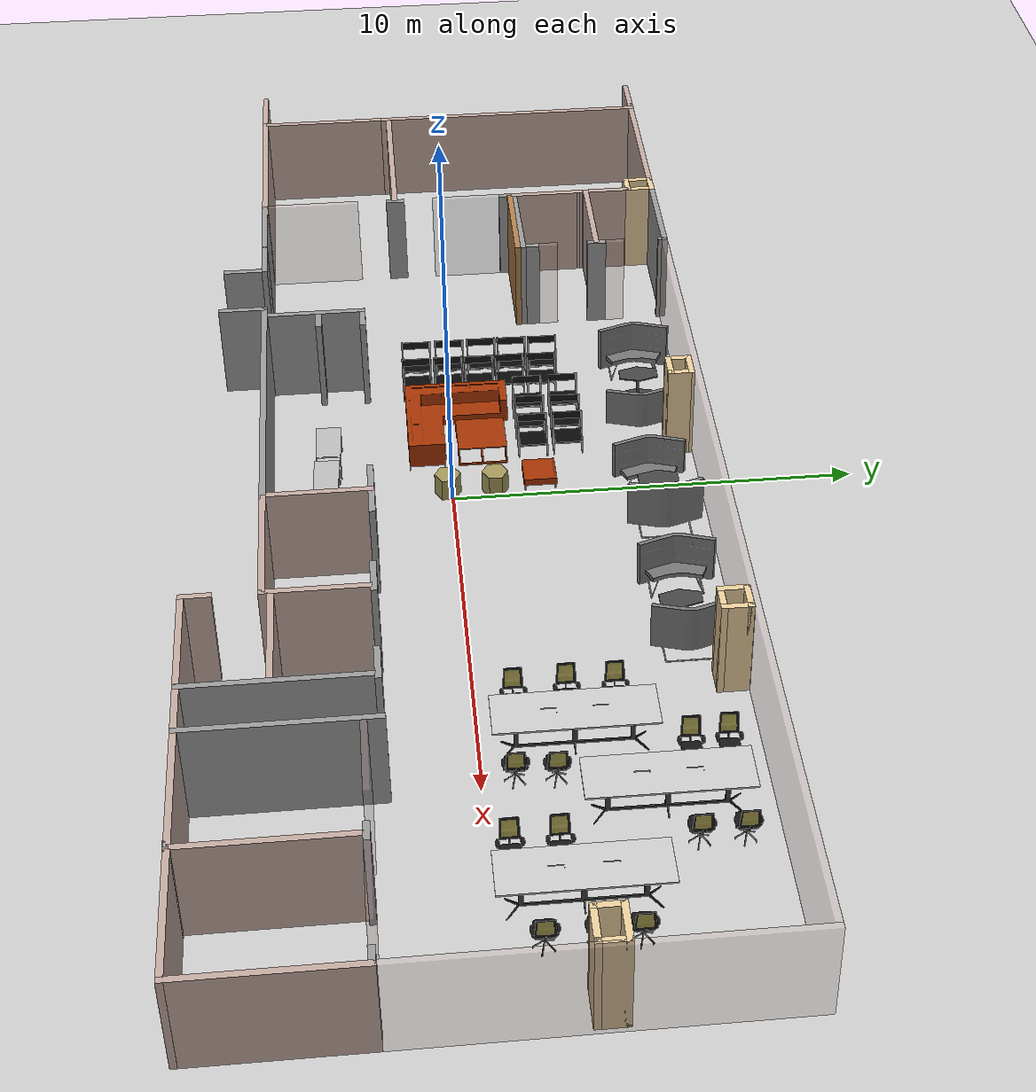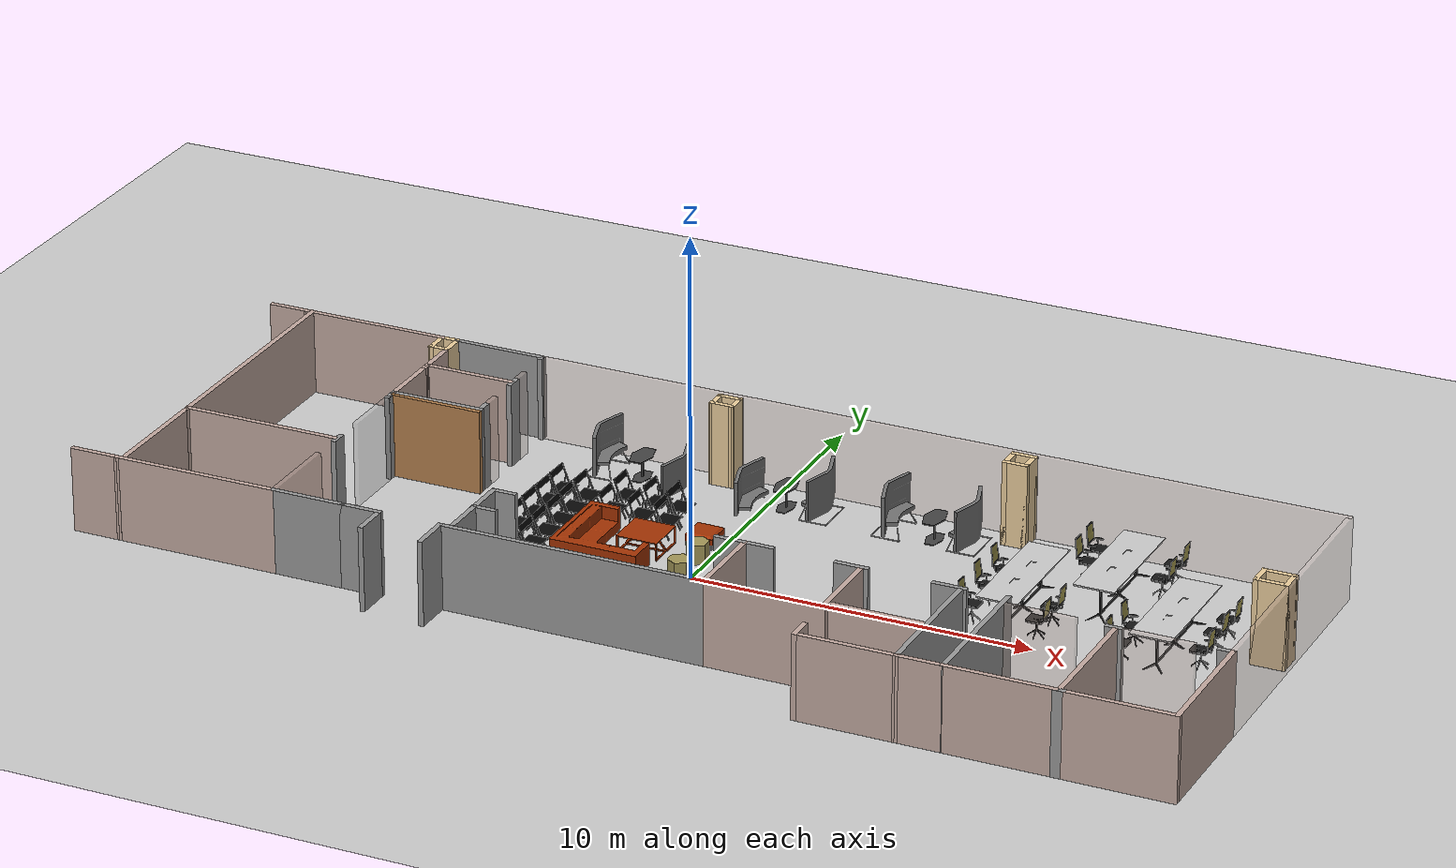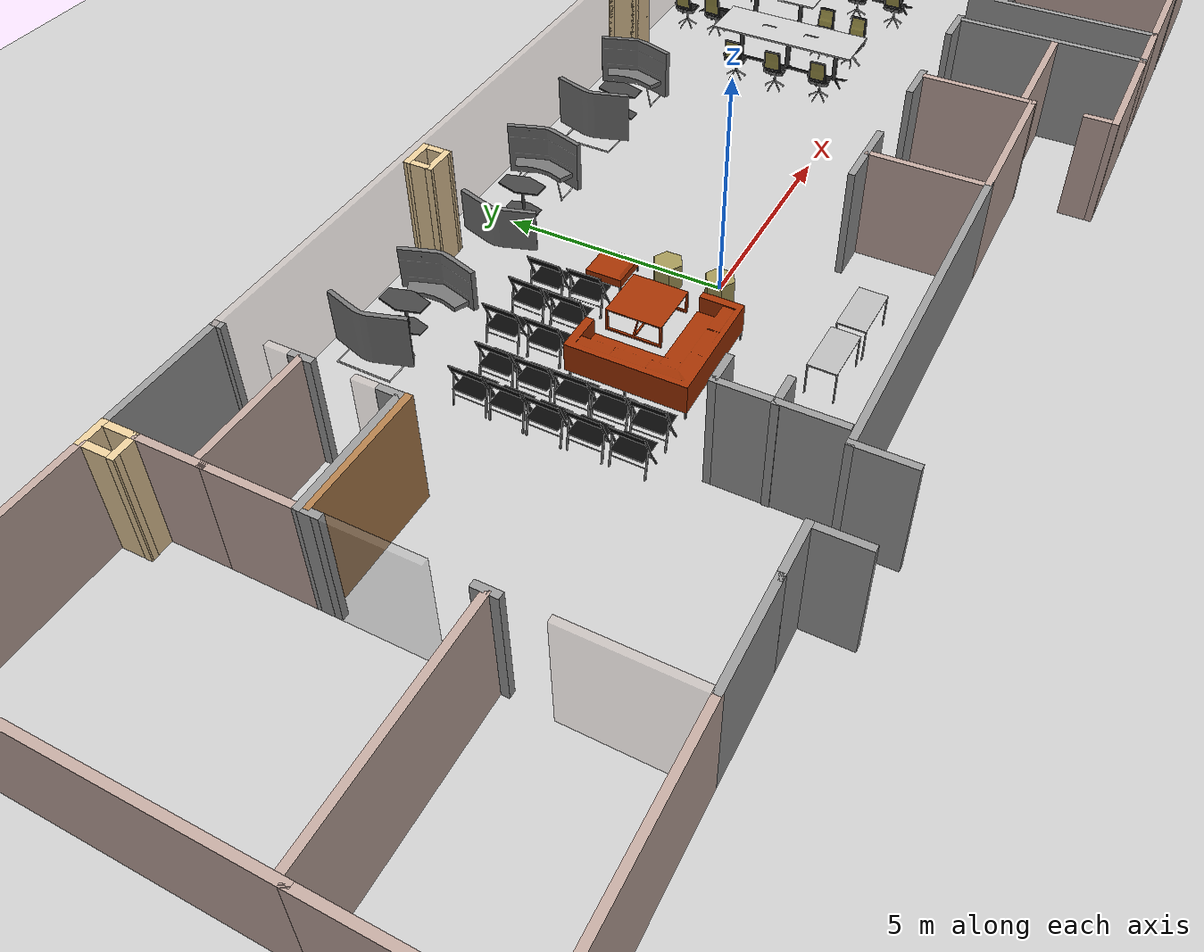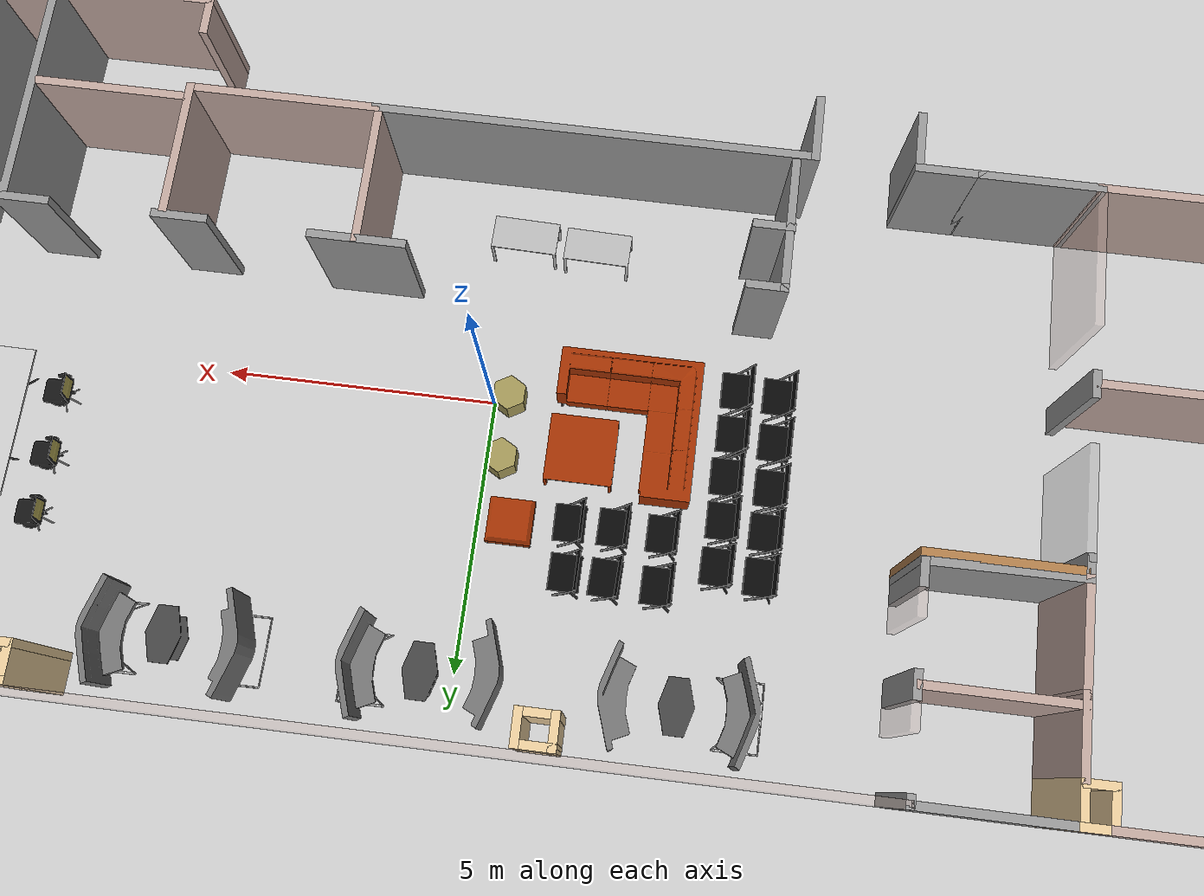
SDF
<?xml version="1.0" ?>
<sdf version="1.4">

  <world name="default">
    <include>
      <uri>model://ground_plane</uri>
    </include>

    <light name='sun' type='directional'>
      <cast_shadows>0</cast_shadows>
      <pose frame=''>0 0 10 0 -0 0</pose>
      <attenuation>
      </attenuation>
      <direction>-0.5 0.1 -0.9</direction>
    </light>

    <include>
      <uri>model://cr2_gazebo/models/ss_austin/austin_office_base</uri>
      <name>austin_office</name>
      <pose>0 0 0 0 0 0</pose>
    </include>

    <include>
      <uri>model://cr2_gazebo/models/ss_austin/sofa</uri>
      <name>sofa</name>
      <pose>-2.474693 0.283700 0.447276 -0.000004 -0.000002 3.140875</pose>
    </include>

    <include>
      <uri>model://cr2_gazebo/models/ss_austin/simple_chair</uri>
      <name>simple_chair_0</name>
      <pose>-1.752816 3.035121 0.458327 0.00 -0.000132 3.134327</pose>
    </include>

    <include>
      <uri>model://cr2_gazebo/models/ss_austin/simple_chair</uri>
      <name>simple_chair_1</name>
      <pose>-1.725184 2.139694 0.458326 -0.000003 -0.000134 -3.130285</pose>
    </include>

    <include>
      <uri>model://cr2_gazebo/models/ss_austin/simple_chair</uri>
      <name>simple_chair_2</name>
      <pose>-2.476814 3.044706 0.458328 0.000001 -0.000132 3.103170</pose>
    </include>

    <include>
      <uri>model://cr2_gazebo/models/ss_austin/simple_chair</uri>
      <name>simple_chair_3</name>
      <pose>-2.517177 2.132703 0.458328 0.000001 -0.000134 3.126198</pose>
    </include>

    <include>
      <uri>model://cr2_gazebo/models/ss_austin/simple_chair</uri>
      <name>simple_chair_4</name>
      <pose>-3.398947 3.074628 0.458329 -0.000003 -0.000134 3.132167</pose>
    </include>

    <include>
      <uri>model://cr2_gazebo/models/ss_austin/simple_chair</uri>
      <name>simple_chair_5</name>
      <pose>-3.394950 2.141943 0.458327 0.00 -0.000132 3.134203</pose>
    </include>

    <include>
      <uri>model://cr2_gazebo/models/ss_austin/simple_chair</uri>
      <name>simple_chair_6</name>
      <pose>-4.401969 2.606460 0.458325 0.000009 -0.000138 3.126337</pose>
    </include>

    <include>
      <uri>model://cr2_gazebo/models/ss_austin/simple_chair</uri>
      <name>simple_chair_7</name>
      <pose>-4.424557 1.771304 0.458328 0.00 -0.000134 -3.138608</pose>
    </include>

    <include>
      <uri>model://cr2_gazebo/models/ss_austin/simple_chair</uri>
      <name>simple_chair_8</name>
      <pose>-4.410206 0.962450 0.458327 0.00 -0.000132 -3.138225</pose>
    </include>

    <include>
      <uri>model://cr2_gazebo/models/ss_austin/simple_chair</uri>
      <name>simple_chair_9</name>
      <pose>-4.445363 0.160832 0.458327 0.00 -0.000132 -3.138929</pose>
    </include>

    <include>
      <uri>model://cr2_gazebo/models/ss_austin/simple_chair</uri>
      <name>simple_chair_10</name>
      <pose>-4.448195 -0.661269 0.458327 0.00 -0.000132 -3.138243</pose>
    </include>

    <include>
      <uri>model://cr2_gazebo/models/ss_austin/simple_chair</uri>
      <name>simple_chair_11</name>
      <pose>-5.183399 2.699501 0.458328 0.000001 -0.000132 3.126669</pose>
    </include>

    <include>
      <uri>model://cr2_gazebo/models/ss_austin/simple_chair</uri>
      <name>simple_chair_12</name>
      <pose>-5.201388 1.885506 0.458328 0.000001 -0.000132 3.126204</pose>
    </include>

    <include>
      <uri>model://cr2_gazebo/models/ss_austin/simple_chair</uri>
      <name>simple_chair_13</name>
      <pose>-5.220889 1.080064 0.458328 0.000001 -0.000132 3.126301</pose>
    </include>

    <include>
      <uri>model://cr2_gazebo/models/ss_austin/simple_chair</uri>
      <name>simple_chair_14</name>
      <pose>-5.212958 0.231431 0.458327 -0.000001 -0.000132 3.126477</pose>
    </include>

    <include>
      <uri>model://cr2_gazebo/models/ss_austin/simple_chair</uri>
      <name>simple_chair_15</name>
      <pose>-5.213259 -0.640615 0.458328 0.000001 -0.000132 3.126367</pose>
    </include>

    <include>
      <uri>model://cr2_gazebo/models/ss_austin/talk_sofa</uri>
      <name>talk_sofa_0</name>
      <pose>-5.171453 5.114709 0.778740 0.000004 0.000002 0.001596</pose>
    </include>

    <include>
      <uri>model://cr2_gazebo/models/ss_austin/talk_sofa</uri>
      <name>talk_sofa_1</name>
      <pose>-2.69869 5.06989 0.365 0 0 -3.12976</pose>
    </include>

    <include>
      <uri>model://cr2_gazebo/models/ss_austin/talk_sofa</uri>
      <name>talk_sofa_2</name>
      <pose>-0.743249 4.9706 0.365 0 -0 0.001606</pose>
    </include>

    <include>
      <uri>model://cr2_gazebo/models/ss_austin/talk_sofa</uri>
      <name>talk_sofa_3</name>
      <pose>6.142236 5.065474 0.778740 0.00 -0.000002 -3.130157</pose>
    </include>

    <include>
      <uri>model://cr2_gazebo/models/ss_austin/talk_sofa</uri>
      <name>talk_sofa_4</name>
      <pose>3.654634 5.031554 0.778743 0.00 0.00 0.001606</pose>
    </include>

    <include>
      <uri>model://cr2_gazebo/models/ss_austin/talk_sofa</uri>
      <name>talk_sofa_5</name>
      <pose>1.707233 5.085215 0.778743 0.00 0.000002 -3.129765</pose>
    </include>

    <include>
      <uri>model://cr2_gazebo/models/ss_austin/talk_table</uri>
      <name>talk_table_0</name>
      <pose>-3.929054 5.112441 0.404065 0.000006 0.000006 3.140211</pose>
    </include>

    <include>
      <uri>model://cr2_gazebo/models/ss_austin/talk_table</uri>
      <name>talk_table_1</name>
      <pose>0.516257 5.052311 0.404063 0.00 0.00 3.139933</pose>
    </include>

    <include>
      <uri>model://cr2_gazebo/models/ss_austin/talk_table</uri>
      <name>talk_table_2</name>
      <pose>5.025823 4.969944 0.404061 0.000010 -0.000006 -3.134065</pose>
    </include>

    <include>
      <uri>model://cr2_gazebo/models/ss_austin/long_table</uri>
      <name>long_table_1</name>
      <pose>13.292382 1.839442 0.610000 0.00 0.00 1.570009</pose>
    </include>

    <include>
      <uri>model://cr2_gazebo/models/ss_austin/long_table</uri>
      <name>long_table_2</name>
      <pose>10.882910 3.873014 0.610000 0.00 0.00 -1.57519</pose>
    </include>

    <include>
      <uri>model://cr2_gazebo/models/ss_austin/long_table</uri>
      <name>long_table_3</name>
      <pose>8.82175 2.112629 0.609995 0.000008 0.00 -1.575189</pose>
    </include>

    <include>
      <uri>model://cr2_gazebo/models/ss_austin/mini_table</uri>
      <name>mini_table</name>
      <pose>-1.52682 0.841662 0.490032 0 -3e-06 3.14018</pose>
    </include>

    <include>
      <uri>model://cr2_gazebo/models/ss_austin/stool</uri>
      <name>stool_1</name>
      <pose>-0.624225 2.19998 0.2 0 -0 3.14018</pose>
    </include>

    <include>
      <uri>model://cr2_gazebo/models/ss_austin/puffy_blue</uri>
      <name>puffy_blue_0</name>
      <pose>-0.3 -0.11 0.290000 0.00 0.00 3.140181</pose>
    </include>

    <include>
      <uri>model://cr2_gazebo/models/ss_austin/puffy_blue</uri>
      <name>puffy_blue_1</name>
      <pose>-0.3 1.07 0.29 0 -0 3.14018</pose>
    </include>

    <include>
      <uri>model://cr2_gazebo/models/ss_austin/table_in_the_kitchen</uri>
      <name>table_in_the_kitchen_1</name>
      <pose>-0.204635 -3.0939 0.5 0 -0 3.11796</pose>
    </include>

    <include>
      <uri>model://cr2_gazebo/models/ss_austin/table_in_the_kitchen</uri>
      <name>table_in_the_kitchen_2</name>
      <pose>-1.56907 -3.02112 0.499997 3e-06 -3e-06 3.11751</pose>
    </include>

    <include>
      <uri>model://cr2_gazebo/models/ss_austin/office_chair_near_white_table</uri>
      <name>office_chair_0</name>
      <pose>7.89232 0.873958 0.59 0 -0 1.58554</pose>
    </include>

    <include>
      <uri>model://cr2_gazebo/models/ss_austin/office_chair_near_white_table</uri>
      <name>office_chair_1</name>
      <pose>7.8549 2.053 0.59 0 -0 1.58585</pose>
    </include>

    <include>
      <uri>model://cr2_gazebo/models/ss_austin/office_chair_near_white_table</uri>
      <name>office_chair_2</name>
      <pose>7.8908 3.13126 0.59 0 -0 1.5854</pose>
    </include>

    <include>
      <uri>model://cr2_gazebo/models/ss_austin/office_chair_near_white_table</uri>
      <name>office_chair_3</name>
      <pose>12.31 0.442557 0.59 0 -0 1.58605</pose>
    </include>

    <include>
      <uri>model://cr2_gazebo/models/ss_austin/office_chair_near_white_table</uri>
      <name>office_chair_4</name>
      <pose>12.3097 1.47774 0.59 0 -0 1.58163</pose>
    </include>

    <include>
      <uri>model://cr2_gazebo/models/ss_austin/office_chair_near_white_table</uri>
      <name>office_chair_5</name>
      <pose>14.3537 0.939361 0.59 0 0 -1.57935</pose>
    </include>

    <include>
      <uri>model://cr2_gazebo/models/ss_austin/office_chair_near_white_table</uri>
      <name>office_chair_6</name>
      <pose>11.9001 5.38199 0.59 0 0 -1.57935</pose>
    </include>

    <include>
      <uri>model://cr2_gazebo/models/ss_austin/office_chair_near_white_table</uri>
      <name>office_chair_7</name>
      <pose>11.8993 4.41126 0.59 0 0 -1.57935</pose>
    </include>

    <include>
      <uri>model://cr2_gazebo/models/ss_austin/office_chair_near_white_table</uri>
      <name>office_chair_8</name>
      <pose>9.75719 4.54106 0.59 0 -0 1.54139</pose>
    </include>

    <include>
      <uri>model://cr2_gazebo/models/ss_austin/office_chair_near_white_table</uri>
      <name>office_chair_9</name>
      <pose>9.73888 5.37214 0.59 0 -0 1.54139</pose>
    </include>

    <include>
      <uri>model://cr2_gazebo/models/ss_austin/office_chair_near_white_table</uri>
      <name>office_chair_10</name>
      <pose>14.3339 2.02488 0.59 0 0 -1.57935</pose>
    </include>

    <include>
      <uri>model://cr2_gazebo/models/ss_austin/office_chair_near_white_table</uri>
      <name>office_chair_11</name>
      <pose>14.3633 2.90135 0.59 0 0 -1.57935</pose>
    </include>

    <include>
      <uri>model://cr2_gazebo/models/ss_austin/office_chair_near_white_table</uri>
      <name>office_chair_12</name>
      <pose>9.776310 0.738197 0.590000 0.00 0.00 -1.579350</pose>
    </include>

    <include>
      <uri>model://cr2_gazebo/models/ss_austin/office_chair_near_white_table</uri>
      <name>office_chair_13</name>
      <pose>9.841594 1.625942 0.5900000 0.00 0.00 -1.579350</pose>
    </include>

    <gui fullscreen='0'>
      <camera name='user_camera'>
        <pose>4.927360 -4.376610 3.740080 0.000000 0.275643 2.356190</pose>
        <view_controller>orbit</view_controller>
      </camera>
    </gui>

  </world>
</sdf>

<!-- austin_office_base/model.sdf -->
<sdf version='1.6'>
  <model name='oa2'>
    <pose frame=''>-0.678371 0.389799 0 0 -0 0</pose>
    <link name='Wall_0'>
      <collision name='Wall_0_Collision'>
        <geometry>
          <box>
            <size>0.75 0.15 2.5</size>
          </box>
        </geometry>
        <pose frame=''>0 0 1.25 0 -0 0</pose>
      </collision>
      <visual name='Wall_0_Visual'>
        <pose frame=''>0 0 1.25 0 -0 0</pose>
        <geometry>
          <box>
            <size>0.75 0.15 2.5</size>
          </box>
        </geometry>
        <material>
          <script>
            <uri>file://media/materials/scripts/gazebo.material</uri>
            <name>Gazebo/Grey</name>
          </script>
          <ambient>0 0 0 1</ambient>
        </material>
        <meta>
          <layer>0</layer>
        </meta>
      </visual>
      <pose frame=''>-4.63163 -1.9898 0 0 -0 3.14159</pose>
    </link>
    <link name='Wall_1'>
      <collision name='Wall_1_Collision'>
        <geometry>
          <box>
            <size>2.5 0.15 2.5</size>
          </box>
        </geometry>
        <pose frame=''>0 0 1.25 0 -0 0</pose>
      </collision>
      <visual name='Wall_1_Visual'>
        <pose frame=''>0 0 1.25 0 -0 0</pose>
        <geometry>
          <box>
            <size>2.5 0.15 2.5</size>
          </box>
        </geometry>
        <material>
          <script>
            <uri>file://media/materials/scripts/gazebo.material</uri>
            <name>Gazebo/Grey</name>
          </script>
          <ambient>0 0 0 1</ambient>
        </material>
        <meta>
          <layer>0</layer>
        </meta>
      </visual>
      <pose frame=''>-4.93163 -3.1648 0 0 0 -1.5708</pose>
    </link>
    <link name='Wall_100'>
      <collision name='Wall_100_Collision'>
        <geometry>
          <box>
            <size>0.366372 0.15 2.5</size>
          </box>
        </geometry>
        <pose frame=''>0 0 1.25 0 -0 0</pose>
      </collision>
      <visual name='Wall_100_Visual'>
        <pose frame=''>0 0 1.25 0 -0 0</pose>
        <geometry>
          <box>
            <size>0.366372 0.15 2.5</size>
          </box>
        </geometry>
        <material>
          <script>
            <uri>file://media/materials/scripts/gazebo.material</uri>
            <name>Gazebo/Grey</name>
          </script>
          <ambient>1 1 1 1</ambient>
        </material>
        <meta>
          <layer>0</layer>
        </meta>
      </visual>
      <pose frame=''>13.2808 -6.2652 0 0 0 -3.11598</pose>
    </link>
    <link name='Wall_102'>
      <collision name='Wall_102_Collision'>
        <geometry>
          <box>
            <size>3.75 0.15 2.5</size>
          </box>
        </geometry>
        <pose frame=''>0 0 1.25 0 -0 0</pose>
      </collision>
      <visual name='Wall_102_Visual'>
        <pose frame=''>0 0 1.25 0 -0 0</pose>
        <geometry>
          <box>
            <size>3.75 0.15 2.5</size>
          </box>
        </geometry>
        <material>
          <script>
            <uri>file://media/materials/scripts/gazebo.material</uri>
            <name>Gazebo/Grey</name>
          </script>
          <ambient>0.760784 0.662745 0.627451 1</ambient>
        </material>
        <meta>
          <layer>0</layer>
        </meta>
      </visual>
      <pose frame=''>13.2718 -4.34355 0 0 0 -1.5708</pose>
    </link>
    <link name='Wall_11'>
      <collision name='Wall_11_Collision'>
        <geometry>
          <box>
            <size>2.5 0.15 2.5</size>
          </box>
        </geometry>
        <pose frame=''>0 0 1.25 0 -0 0</pose>
      </collision>
      <visual name='Wall_11_Visual'>
        <pose frame=''>0 0 1.25 0 -0 0</pose>
        <geometry>
          <box>
            <size>2.5 0.15 2.5</size>
          </box>
        </geometry>
        <material>
          <script>
            <uri>file://media/materials/scripts/gazebo.material</uri>
            <name>Gazebo/Grey</name>
          </script>
          <ambient>0.760784 0.662745 0.627451 1</ambient>
        </material>
        <meta>
          <layer>0</layer>
        </meta>
      </visual>
      <pose frame=''>2.52759 -3.18022 0 0 0 -1.5708</pose>
    </link>
    <link name='Wall_110'>
      <collision name='Wall_110_Collision'>
        <geometry>
          <box>
            <size>3.25 0.15 2.5</size>
          </box>
        </geometry>
        <pose frame=''>0 0 1.25 0 -0 0</pose>
      </collision>
      <visual name='Wall_110_Visual'>
        <pose frame=''>0 0 1.25 0 -0 0</pose>
        <geometry>
          <box>
            <size>3.25 0.15 2.5</size>
          </box>
        </geometry>
        <material>
          <script>
            <uri>file://media/materials/scripts/gazebo.material</uri>
            <name>Gazebo/Grey</name>
          </script>
          <ambient>0.760784 0.662745 0.627451 1</ambient>
        </material>
        <meta>
          <layer>0</layer>
        </meta>
      </visual>
      <pose frame=''>11.6313 -6.25931 0 0 -0 0</pose>
    </link>
    <link name='Wall_113'>
      <collision name='Wall_113_Collision'>
        <geometry>
          <box>
            <size>1.45217 0.15 2.5</size>
          </box>
        </geometry>
        <pose frame=''>0 0 1.25 0 -0 0</pose>
      </collision>
      <visual name='Wall_113_Visual'>
        <pose frame=''>0 0 1.25 0 -0 0</pose>
        <geometry>
          <box>
            <size>1.45217 0.15 2.5</size>
          </box>
        </geometry>
        <material>
          <script>
            <uri>file://media/materials/scripts/gazebo.material</uri>
            <name>Gazebo/Grey</name>
          </script>
          <ambient>0.760784 0.662745 0.627451 1</ambient>
        </material>
        <meta>
          <layer>0</layer>
        </meta>
      </visual>
      <pose frame=''>9.43019 -6.26045 0 0 -0 0.001756</pose>
    </link>
    <link name='Wall_116'>
      <collision name='Wall_116_Collision'>
        <geometry>
          <box>
            <size>4.40779 0.15 2.5</size>
          </box>
        </geometry>
        <pose frame=''>0 0 1.25 0 -0 0</pose>
      </collision>
      <visual name='Wall_116_Visual'>
        <pose frame=''>0 0 1.25 0 -0 0</pose>
        <geometry>
          <box>
            <size>4.40779 0.15 2.5</size>
          </box>
        </geometry>
        <material>
          <script>
            <uri>file://media/materials/scripts/gazebo.material</uri>
            <name>Gazebo/Grey</name>
          </script>
          <ambient>0 0 0 1</ambient>
        </material>
        <meta>
          <layer>0</layer>
        </meta>
      </visual>
      <pose frame=''>10.0806 -4.13042 0 0 0 -1.57049</pose>
    </link>
    <link name='Wall_118'>
      <collision name='Wall_118_Collision'>
        <geometry>
          <box>
            <size>4.25 0.15 2.5</size>
          </box>
        </geometry>
        <pose frame=''>0 0 1.25 0 -0 0</pose>
      </collision>
      <visual name='Wall_118_Visual'>
        <pose frame=''>0 0 1.25 0 -0 0</pose>
        <geometry>
          <box>
            <size>4.25 0.15 2.5</size>
          </box>
        </geometry>
        <material>
          <script>
            <uri>file://media/materials/scripts/gazebo.material</uri>
            <name>Gazebo/Grey</name>
          </script>
          <ambient>0 0 0 1</ambient>
        </material>
        <meta>
          <layer>0</layer>
        </meta>
      </visual>
      <pose frame=''>8.78475 -4.2116 0 0 0 -1.5708</pose>
    </link>
    <link name='Wall_120'>
      <collision name='Wall_120_Collision'>
        <geometry>
          <box>
            <size>1 0.15 2.5</size>
          </box>
        </geometry>
        <pose frame=''>0 0 1.25 0 -0 0</pose>
      </collision>
      <visual name='Wall_120_Visual'>
        <pose frame=''>0 0 1.25 0 -0 0</pose>
        <geometry>
          <box>
            <size>1 0.15 2.5</size>
          </box>
        </geometry>
        <material>
          <script>
            <uri>file://media/materials/scripts/gazebo.material</uri>
            <name>Gazebo/Grey</name>
          </script>
          <ambient>0 0 0 1</ambient>
        </material>
        <meta>
          <layer>0</layer>
        </meta>
      </visual>
      <pose frame=''>8.44693 -2.03935 0 0 -0 0</pose>
    </link>
    <link name='Wall_122'>
      <collision name='Wall_122_Collision'>
        <geometry>
          <box>
            <size>1 0.15 2.5</size>
          </box>
        </geometry>
        <pose frame=''>0 0 1.25 0 -0 0</pose>
      </collision>
      <visual name='Wall_122_Visual'>
        <pose frame=''>0 0 1.25 0 -0 0</pose>
        <geometry>
          <box>
            <size>1 0.15 2.5</size>
          </box>
        </geometry>
        <material>
          <script>
            <uri>file://media/materials/scripts/gazebo.material</uri>
            <name>Gazebo/Grey</name>
          </script>
          <ambient>0 0 0 1</ambient>
        </material>
        <meta>
          <layer>0</layer>
        </meta>
      </visual>
      <pose frame=''>5.64113 -2.03506 0 0 -0 3.14159</pose>
    </link>
    <link name='Wall_124'>
      <collision name='Wall_124_Collision'>
        <geometry>
          <box>
            <size>2.75 0.15 2.5</size>
          </box>
        </geometry>
        <pose frame=''>0 0 1.25 0 -0 0</pose>
      </collision>
      <visual name='Wall_124_Visual'>
        <pose frame=''>0 0 1.25 0 -0 0</pose>
        <geometry>
          <box>
            <size>2.75 0.15 2.5</size>
          </box>
        </geometry>
        <material>
          <script>
            <uri>file://media/materials/scripts/gazebo.material</uri>
            <name>Gazebo/Grey</name>
          </script>
          <ambient>0.760784 0.662745 0.627451 1</ambient>
        </material>
        <meta>
          <layer>0</layer>
        </meta>
      </visual>
      <pose frame=''>7.35645 -4.30687 0 0 -0 3.14159</pose>
    </link>
    <link name='Wall_126'>
      <collision name='Wall_126_Collision'>
        <geometry>
          <box>
            <size>2.5 0.15 2.5</size>
          </box>
        </geometry>
        <pose frame=''>0 0 1.25 0 -0 0</pose>
      </collision>
      <visual name='Wall_126_Visual'>
        <pose frame=''>0 0 1.25 0 -0 0</pose>
        <geometry>
          <box>
            <size>2.5 0.15 2.5</size>
          </box>
        </geometry>
        <material>
          <script>
            <uri>file://media/materials/scripts/gazebo.material</uri>
            <name>Gazebo/Grey</name>
          </script>
          <ambient>0.760784 0.662745 0.627451 1</ambient>
        </material>
        <meta>
          <layer>0</layer>
        </meta>
      </visual>
      <pose frame=''>5.94317 -3.32964 0 0 -0 1.5708</pose>
    </link>
    <link name='Wall_128'>
      <collision name='Wall_128_Collision'>
        <geometry>
          <box>
            <size>3.5 0.15 2.5</size>
          </box>
        </geometry>
        <pose frame=''>0 0 1.25 0 -0 0</pose>
      </collision>
      <visual name='Wall_128_Visual'>
        <pose frame=''>0 0 1.25 0 -0 0</pose>
        <geometry>
          <box>
            <size>3.5 0.15 2.5</size>
          </box>
        </geometry>
        <material>
          <script>
            <uri>file://media/materials/scripts/gazebo.material</uri>
            <name>Gazebo/Grey</name>
          </script>
          <ambient>0.760784 0.662745 0.627451 1</ambient>
        </material>
        <meta>
          <layer>0</layer>
        </meta>
      </visual>
      <pose frame=''>4.26817 -4.50464 0 0 -0 0</pose>
    </link>

    <link name='Wall_136'>
      <collision name='Wall_136_Collision'>
        <geometry>
          <box>
            <size>1.25 0.15 2.5</size>
          </box>
        </geometry>
        <pose frame=''>0 0 1.25 0 -0 0</pose>
      </collision>
      <visual name='Wall_136_Visual'>
        <pose frame=''>0 0 1.25 0 -0 0</pose>
        <geometry>
          <box>
            <size>1.25 0.15 2.5</size>
          </box>
        </geometry>
        <material>
          <script>
            <uri>file://media/materials/scripts/gazebo.material</uri>
            <name>Gazebo/Grey</name>
          </script>
          <ambient>0 0 0 1</ambient>
        </material>
        <meta>
          <layer>0</layer>
        </meta>
      </visual>
      <pose frame=''>-5.25683 -5.05464 0 0 0 -1.5708</pose>
    </link>
    <link name='Wall_14'>
      <collision name='Wall_14_Collision'>
        <geometry>
          <box>
            <size>3.5 0.15 2.5</size>
          </box>
        </geometry>
        <pose frame=''>0 0 1.25 0 -0 0</pose>
      </collision>
      <visual name='Wall_14_Visual'>
        <pose frame=''>0 0 1.25 0 -0 0</pose>
        <geometry>
          <box>
            <size>3.5 0.15 2.5</size>
          </box>
        </geometry>
        <material>
          <script>
            <uri>file://media/materials/scripts/gazebo.material</uri>
            <name>Gazebo/Grey</name>
          </script>
          <ambient>1 1 1 1</ambient>
        </material>
        <meta>
          <layer>0</layer>
        </meta>
      </visual>
      <pose frame=''>4.26817 -4.50464 0 0 -0 0</pose>
    </link>
    <link name='Wall_140'>
      <collision name='Wall_140_Collision'>
        <geometry>
          <box>
            <size>0.15 0.15 2.5</size>
          </box>
        </geometry>
        <pose frame=''>0 0 1.25 0 -0 0</pose>
      </collision>
      <visual name='Wall_140_Visual'>
        <pose frame=''>0 0 1.25 0 -0 0</pose>
        <geometry>
          <box>
            <size>0.15 0.15 2.5</size>
          </box>
        </geometry>
        <material>
          <script>
            <uri>file://media/materials/scripts/gazebo.material</uri>
            <name>Gazebo/Grey</name>
          </script>
          <ambient>0 0 0 1</ambient>
        </material>
        <meta>
          <layer>0</layer>
        </meta>
      </visual>
      <pose frame=''>-8.18351 -4.51172 0 0 -0 0</pose>
    </link>
    <link name='Wall_142'>
      <collision name='Wall_142_Collision'>
        <geometry>
          <box>
            <size>2.25 0.15 2.5</size>
          </box>
        </geometry>
        <pose frame=''>0 0 1.25 0 -0 0</pose>
      </collision>
      <visual name='Wall_142_Visual'>
        <pose frame=''>0 0 1.25 0 -0 0</pose>
        <geometry>
          <box>
            <size>2.25 0.15 2.5</size>
          </box>
        </geometry>
        <material>
          <script>
            <uri>file://media/materials/scripts/gazebo.material</uri>
            <name>Gazebo/Grey</name>
          </script>
          <ambient>0 0 0 1</ambient>
        </material>
        <meta>
          <layer>0</layer>
        </meta>
      </visual>
      <pose frame=''>-9.23351 -4.51172 0 0 -0 0</pose>
    </link>
    <link name='Wall_143'>
      <collision name='Wall_143_Collision'>
        <geometry>
          <box>
            <size>1.25 0.15 2.5</size>
          </box>
        </geometry>
        <pose frame=''>0 0 1.25 0 -0 0</pose>
      </collision>
      <visual name='Wall_143_Visual'>
        <pose frame=''>0 0 1.25 0 -0 0</pose>
        <geometry>
          <box>
            <size>1.25 0.15 2.5</size>
          </box>
        </geometry>
        <material>
          <script>
            <uri>file://media/materials/scripts/gazebo.material</uri>
            <name>Gazebo/Grey</name>
          </script>
          <ambient>0 0 0 1</ambient>
        </material>
        <meta>
          <layer>0</layer>
        </meta>
      </visual>
      <pose frame=''>-7.63351 -4.51172 0 0 -0 0</pose>
    </link>
    <link name='Wall_145'>
      <collision name='Wall_145_Collision'>
        <geometry>
          <box>
            <size>3 0.15 2.5</size>
          </box>
        </geometry>
        <pose frame=''>0 0 1.25 0 -0 0</pose>
      </collision>
      <visual name='Wall_145_Visual'>
        <pose frame=''>0 0 1.25 0 -0 0</pose>
        <geometry>
          <box>
            <size>3 0.15 2.5</size>
          </box>
        </geometry>
        <material>
          <script>
            <uri>file://media/materials/scripts/gazebo.material</uri>
            <name>Gazebo/Grey</name>
          </script>
          <ambient>0.760784 0.662745 0.627451 1</ambient>
        </material>
        <meta>
          <layer>0</layer>
        </meta>
      </visual>
      <pose frame=''>7.35975 -6.2616 0 0 -0 3.14159</pose>
    </link>
    <link name='Wall_146'>
      <collision name='Wall_146_Collision'>
        <geometry>
          <box>
            <size>0.75 0.15 2.5</size>
          </box>
        </geometry>
        <pose frame=''>0 0 1.25 0 -0 0</pose>
      </collision>
      <visual name='Wall_146_Visual'>
        <pose frame=''>0 0 1.25 0 -0 0</pose>
        <geometry>
          <box>
            <size>0.75 0.15 2.5</size>
          </box>
        </geometry>
        <material>
          <script>
            <uri>file://media/materials/scripts/gazebo.material</uri>
            <name>Gazebo/Grey</name>
          </script>
          <ambient>0.760784 0.662745 0.627451 1</ambient>
        </material>
        <meta>
          <layer>0</layer>
        </meta>
      </visual>
      <pose frame=''>5.93475 -5.9616 0 0 -0 1.5708</pose>
    </link>
    <link name='Wall_148'>
      <collision name='Wall_148_Collision'>
        <geometry>
          <box>
            <size>2 0.15 2.5</size>
          </box>
        </geometry>
        <pose frame=''>0 0 1.25 0 -0 0</pose>
      </collision>
      <visual name='Wall_148_Visual'>
        <pose frame=''>0 0 1.25 0 -0 0</pose>
        <geometry>
          <box>
            <size>2 0.15 2.5</size>
          </box>
        </geometry>
        <material>
          <script>
            <uri>file://media/materials/scripts/gazebo.material</uri>
            <name>Gazebo/Grey</name>
          </script>
          <ambient>0.760784 0.662745 0.627451 1</ambient>
        </material>
        <meta>
          <layer>0</layer>
        </meta>
        <transparency>0.7</transparency>
      </visual>
      <pose frame=''>11.1562 -2.38788 0 0 -0 0</pose>
    </link>
    <link name='Wall_150'>
      <collision name='Wall_150_Collision'>
        <geometry>
          <box>
            <size>0.5 0.15 2.5</size>
          </box>
        </geometry>
        <pose frame=''>0 0 1.25 0 -0 0</pose>
      </collision>
      <visual name='Wall_150_Visual'>
        <pose frame=''>0 0 1.25 0 -0 0</pose>
        <geometry>
          <box>
            <size>0.5 0.15 2.5</size>
          </box>
        </geometry>
        <material>
          <script>
            <uri>file://media/materials/scripts/gazebo.material</uri>
            <name>Gazebo/Grey</name>
          </script>
          <ambient>0 0 0 1</ambient>
        </material>
        <meta>
          <layer>0</layer>
        </meta>
      </visual>
      <pose frame=''>13.2138 -2.41724 0 0 -0 0</pose>
    </link>
    <link name='Wall_154'>
      <collision name='Wall_154_Collision'>
        <geometry>
          <box>
            <size>0.75 0.15 2.5</size>
          </box>
        </geometry>
        <pose frame=''>0 0 1.25 0 -0 0</pose>
      </collision>
      <visual name='Wall_154_Visual'>
        <pose frame=''>0 0 1.25 0 -0 0</pose>
        <geometry>
          <box>
            <size>0.75 0.15 2.5</size>
          </box>
        </geometry>
        <material>
          <script>
            <uri>file://media/materials/scripts/gazebo.material</uri>
            <name>Gazebo/Grey</name>
          </script>
          <ambient>0.921569 0.807843 0.615686 1</ambient>
        </material>
        <meta>
          <layer>0</layer>
        </meta>
      </visual>
      <pose frame=''>-1.6868 6.09715 0 0 -0 0</pose>
    </link>
    <link name='Wall_155'>
      <collision name='Wall_155_Collision'>
        <geometry>
          <box>
            <size>0.663879 0.15 2.5</size>
          </box>
        </geometry>
        <pose frame=''>0 0 1.25 0 -0 0</pose>
      </collision>
      <visual name='Wall_155_Visual'>
        <pose frame=''>0 0 1.25 0 -0 0</pose>
        <geometry>
          <box>
            <size>0.663879 0.15 2.5</size>
          </box>
        </geometry>
        <material>
          <script>
            <uri>file://media/materials/scripts/gazebo.material</uri>
            <name>Gazebo/Grey</name>
          </script>
          <ambient>0.921569 0.807843 0.615686 1</ambient>
        </material>
        <meta>
          <layer>0</layer>
        </meta>
      </visual>
      <pose frame=''>-1.38372 5.84021 0 0 0 -1.55883</pose>
    </link>
    <link name='Wall_156'>
      <collision name='Wall_156_Collision'>
        <geometry>
          <box>
            <size>0.75 0.15 2.5</size>
          </box>
        </geometry>
        <pose frame=''>0 0 1.25 0 -0 0</pose>
      </collision>
      <visual name='Wall_156_Visual'>
        <pose frame=''>0 0 1.25 0 -0 0</pose>
        <geometry>
          <box>
            <size>0.75 0.15 2.5</size>
          </box>
        </geometry>
        <material>
          <script>
            <uri>file://media/materials/scripts/gazebo.material</uri>
            <name>Gazebo/Grey</name>
          </script>
          <ambient>0.921569 0.807843 0.615686 1</ambient>
        </material>
        <meta>
          <layer>0</layer>
        </meta>
      </visual>
      <pose frame=''>-1.6868 5.58326 0 0 -0 3.14159</pose>
    </link>
    <link name='Wall_157'>
      <collision name='Wall_157_Collision'>
        <geometry>
          <box>
            <size>0.663879 0.15 2.5</size>
          </box>
        </geometry>
        <pose frame=''>0 0 1.25 0 -0 0</pose>
      </collision>
      <visual name='Wall_157_Visual'>
        <pose frame=''>0 0 1.25 0 -0 0</pose>
        <geometry>
          <box>
            <size>0.663879 0.15 2.5</size>
          </box>
        </geometry>
        <material>
          <script>
            <uri>file://media/materials/scripts/gazebo.material</uri>
            <name>Gazebo/Grey</name>
          </script>
          <ambient>0.921569 0.807843 0.615686 1</ambient>
        </material>
        <meta>
          <layer>0</layer>
        </meta>
      </visual>
      <pose frame=''>-1.98372 5.84021 0 0 -0 1.58277</pose>
    </link>
    <link name='Wall_159'>
      <collision name='Wall_159_Collision'>
        <geometry>
          <box>
            <size>0.75 0.15 2.5</size>
          </box>
        </geometry>
        <pose frame=''>0 0 1.25 0 -0 0</pose>
      </collision>
      <visual name='Wall_159_Visual'>
        <pose frame=''>0 0 1.25 0 -0 0</pose>
        <geometry>
          <box>
            <size>0.75 0.15 2.5</size>
          </box>
        </geometry>
        <material>
          <script>
            <uri>file://media/materials/scripts/gazebo.material</uri>
            <name>Gazebo/Grey</name>
          </script>
          <ambient>0.921569 0.807843 0.615686 1</ambient>
        </material>
        <meta>
          <layer>0</layer>
        </meta>
      </visual>
      <pose frame=''>7.14671 6.12175 0 0 -0 0</pose>
    </link>
    <link name='Wall_160'>
      <collision name='Wall_160_Collision'>
        <geometry>
          <box>
            <size>0.75 0.15 2.5</size>
          </box>
        </geometry>
        <pose frame=''>0 0 1.25 0 -0 0</pose>
      </collision>
      <visual name='Wall_160_Visual'>
        <pose frame=''>0 0 1.25 0 -0 0</pose>
        <geometry>
          <box>
            <size>0.75 0.15 2.5</size>
          </box>
        </geometry>
        <material>
          <script>
            <uri>file://media/materials/scripts/gazebo.material</uri>
            <name>Gazebo/Grey</name>
          </script>
          <ambient>0.921569 0.807843 0.615686 1</ambient>
        </material>
        <meta>
          <layer>0</layer>
        </meta>
      </visual>
      <pose frame=''>7.44671 5.82175 0 0 0 -1.5708</pose>
    </link>
    <link name='Wall_161'>
      <collision name='Wall_161_Collision'>
        <geometry>
          <box>
            <size>0.75 0.15 2.5</size>
          </box>
        </geometry>
        <pose frame=''>0 0 1.25 0 -0 0</pose>
      </collision>
      <visual name='Wall_161_Visual'>
        <pose frame=''>0 0 1.25 0 -0 0</pose>
        <geometry>
          <box>
            <size>0.75 0.15 2.5</size>
          </box>
        </geometry>
        <material>
          <script>
            <uri>file://media/materials/scripts/gazebo.material</uri>
            <name>Gazebo/Grey</name>
          </script>
          <ambient>0.921569 0.807843 0.615686 1</ambient>
        </material>
        <meta>
          <layer>0</layer>
        </meta>
      </visual>
      <pose frame=''>7.14671 5.52175 0 0 -0 3.14159</pose>
    </link>
    <link name='Wall_162'>
      <collision name='Wall_162_Collision'>
        <geometry>
          <box>
            <size>0.75 0.15 2.5</size>
          </box>
        </geometry>
        <pose frame=''>0 0 1.25 0 -0 0</pose>
      </collision>
      <visual name='Wall_162_Visual'>
        <pose frame=''>0 0 1.25 0 -0 0</pose>
        <geometry>
          <box>
            <size>0.75 0.15 2.5</size>
          </box>
        </geometry>
        <material>
          <script>
            <uri>file://media/materials/scripts/gazebo.material</uri>
            <name>Gazebo/Grey</name>
          </script>
          <ambient>0.921569 0.807843 0.615686 1</ambient>
        </material>
        <meta>
          <layer>0</layer>
        </meta>
      </visual>
      <pose frame=''>6.84671 5.82175 0 0 -0 1.5708</pose>
    </link>
    <link name='Wall_164'>
      <collision name='Wall_164_Collision'>
        <geometry>
          <box>
            <size>1 0.15 2.5</size>
          </box>
        </geometry>
        <pose frame=''>0 0 1.25 0 -0 0</pose>
      </collision>
      <visual name='Wall_164_Visual'>
        <pose frame=''>0 0 1.25 0 -0 0</pose>
        <geometry>
          <box>
            <size>1 0.15 2.5</size>
          </box>
        </geometry>
        <material>
          <script>
            <uri>file://media/materials/scripts/gazebo.material</uri>
            <name>Gazebo/Grey</name>
          </script>
          <ambient>0.921569 0.807843 0.615686 1</ambient>
        </material>
        <meta>
          <layer>0</layer>
        </meta>
      </visual>
      <pose frame=''>15.9667 2.34904 0 0 -0 0</pose>
    </link>
    <link name='Wall_165'>
      <collision name='Wall_165_Collision'>
        <geometry>
          <box>
            <size>0.75 0.15 2.5</size>
          </box>
        </geometry>
        <pose frame=''>0 0 1.25 0 -0 0</pose>
      </collision>
      <visual name='Wall_165_Visual'>
        <pose frame=''>0 0 1.25 0 -0 0</pose>
        <geometry>
          <box>
            <size>0.75 0.15 2.5</size>
          </box>
        </geometry>
        <material>
          <script>
            <uri>file://media/materials/scripts/gazebo.material</uri>
            <name>Gazebo/Grey</name>
          </script>
          <ambient>0.921569 0.807843 0.615686 1</ambient>
        </material>
        <meta>
          <layer>0</layer>
        </meta>
      </visual>
      <pose frame=''>16.3917 2.04904 0 0 0 -1.5708</pose>
    </link>
    <link name='Wall_166'>
      <collision name='Wall_166_Collision'>
        <geometry>
          <box>
            <size>1 0.15 2.5</size>
          </box>
        </geometry>
        <pose frame=''>0 0 1.25 0 -0 0</pose>
      </collision>
      <visual name='Wall_166_Visual'>
        <pose frame=''>0 0 1.25 0 -0 0</pose>
        <geometry>
          <box>
            <size>1 0.15 2.5</size>
          </box>
        </geometry>
        <material>
          <script>
            <uri>file://media/materials/scripts/gazebo.material</uri>
            <name>Gazebo/Grey</name>
          </script>
          <ambient>0.921569 0.807843 0.615686 1</ambient>
        </material>
        <meta>
          <layer>0</layer>
        </meta>
      </visual>
      <pose frame=''>15.9667 1.74904 0 0 -0 3.14159</pose>
    </link>
    <link name='Wall_167'>
      <collision name='Wall_167_Collision'>
        <geometry>
          <box>
            <size>0.75 0.15 2.5</size>
          </box>
        </geometry>
        <pose frame=''>0 0 1.25 0 -0 0</pose>
      </collision>
      <visual name='Wall_167_Visual'>
        <pose frame=''>0 0 1.25 0 -0 0</pose>
        <geometry>
          <box>
            <size>0.75 0.15 2.5</size>
          </box>
        </geometry>
        <material>
          <script>
            <uri>file://media/materials/scripts/gazebo.material</uri>
            <name>Gazebo/Grey</name>
          </script>
          <ambient>0.921569 0.807843 0.615686 1</ambient>
        </material>
        <meta>
          <layer>0</layer>
        </meta>
      </visual>
      <pose frame=''>15.5417 2.04904 0 0 -0 1.5708</pose>
    </link>
    <link name='Wall_171'>
      <collision name='Wall_171_Collision'>
        <geometry>
          <box>
            <size>1.5 0.15 2.5</size>
          </box>
        </geometry>
        <pose frame=''>0 0 1.25 0 -0 0</pose>
      </collision>
      <visual name='Wall_171_Visual'>
        <pose frame=''>0 0 1.25 0 -0 0</pose>
        <geometry>
          <box>
            <size>1.5 0.15 2.5</size>
          </box>
        </geometry>
        <material>
          <script>
            <uri>file://media/materials/scripts/gazebo.material</uri>
            <name>Gazebo/Grey</name>
          </script>
          <ambient>0.760784 0.662745 0.627451 1</ambient>
        </material>
        <meta>
          <layer>0</layer>
        </meta>
      </visual>
      <pose frame=''>-15.8139 -4.52516 0 0 -0 0</pose>
    </link>
    <link name='Wall_173'>
      <collision name='Wall_173_Collision'>
        <geometry>
          <box>
            <size>2 0.15 2.5</size>
          </box>
        </geometry>
        <pose frame=''>0 0 1.25 0 -0 0</pose>
      </collision>
      <visual name='Wall_173_Visual'>
        <pose frame=''>0 0 1.25 0 -0 0</pose>
        <geometry>
          <box>
            <size>2 0.15 2.5</size>
          </box>
        </geometry>
        <material>
          <script>
            <uri>file://media/materials/scripts/gazebo.material</uri>
            <name>Gazebo/Grey</name>
          </script>
          <ambient>0.760784 0.662745 0.627451 1</ambient>
        </material>
        <meta>
          <layer>0</layer>
        </meta>
        <transparency>0.7</transparency>
      </visual>
      <pose frame=''>14.4632 -2.417 0 0 -0 3.14159</pose>
    </link>
    <link name='Wall_176'>
      <collision name='Wall_176_Collision'>
        <geometry>
          <box>
            <size>0.5 0.15 2.5</size>
          </box>
        </geometry>
        <pose frame=''>0 0 1.25 0 -0 0</pose>
      </collision>
      <visual name='Wall_176_Visual'>
        <pose frame=''>0 0 1.25 0 -0 0</pose>
        <geometry>
          <box>
            <size>0.5 0.15 2.5</size>
          </box>
        </geometry>
        <material>
          <script>
            <uri>file://media/materials/scripts/gazebo.material</uri>
            <name>Gazebo/Grey</name>
          </script>
          <ambient>0 0 0 1</ambient>
        </material>
        <meta>
          <layer>0</layer>
        </meta>
      </visual>
      <pose frame=''>-7.60887 2.60058 0 0 0 -1.5708</pose>
    </link>
    <link name='Wall_178'>
      <collision name='Wall_178_Collision'>
        <geometry>
          <box>
            <size>0.5 0.15 2.5</size>
          </box>
        </geometry>
        <pose frame=''>0 0 1.25 0 -0 0</pose>
      </collision>
      <visual name='Wall_178_Visual'>
        <pose frame=''>0 0 1.25 0 -0 0</pose>
        <geometry>
          <box>
            <size>0.5 0.15 2.5</size>
          </box>
        </geometry>
        <material>
          <script>
            <uri>file://media/materials/scripts/gazebo.material</uri>
            <name>Gazebo/Grey</name>
          </script>
          <ambient>0.760784 0.662745 0.627451 1</ambient>
        </material>
        <meta>
          <layer>0</layer>
        </meta>
        <transparency>0.7</transparency>
      </visual>
      <pose frame=''>-7.60925 3.1 0 0 0 -1.5708</pose>
    </link>
    <link name='Wall_18'>
      <collision name='Wall_18_Collision'>
        <geometry>
          <box>
            <size>8 0.15 2.5</size>
          </box>
        </geometry>
        <pose frame=''>0 0 1.25 0 -0 0</pose>
      </collision>
      <visual name='Wall_18_Visual'>
        <pose frame=''>0 0 1.25 0 -0 0</pose>
        <geometry>
          <box>
            <size>8 0.15 2.5</size>
          </box>
        </geometry>
        <material>
          <script>
            <uri>file://media/materials/scripts/gazebo.material</uri>
            <name>Gazebo/Grey</name>
          </script>
          <ambient>0 0 0 1</ambient>
        </material>
        <meta>
          <layer>0</layer>
        </meta>
      </visual>
      <pose frame=''>-1.33183 -4.50464 0 0 -0 3.14159</pose>
    </link>
    <link name='Wall_180'>
      <collision name='Wall_180_Collision'>
        <geometry>
          <box>
            <size>0.5 0.15 2.5</size>
          </box>
        </geometry>
        <pose frame=''>0 0 1.25 0 -0 0</pose>
      </collision>
      <visual name='Wall_180_Visual'>
        <pose frame=''>0 0 1.25 0 -0 0</pose>
        <geometry>
          <box>
            <size>0.5 0.15 2.5</size>
          </box>
        </geometry>
        <material>
          <script>
            <uri>file://media/materials/scripts/gazebo.material</uri>
            <name>Gazebo/Grey</name>
          </script>
          <ambient>0.760784 0.662745 0.627451 1</ambient>
        </material>
        <meta>
          <layer>0</layer>
        </meta>
        <transparency>0.7</transparency>
      </visual>
      <pose frame=''>-7.60842 4.90901 0 0 0 -1.5708</pose>
    </link>
    <link name='Wall_184'>
      <collision name='Wall_184_Collision'>
        <geometry>
          <box>
            <size>1 0.15 2.5</size>
          </box>
        </geometry>
        <pose frame=''>0 0 1.25 0 -0 0</pose>
      </collision>
      <visual name='Wall_184_Visual'>
        <pose frame=''>0 0 1.25 0 -0 0</pose>
        <geometry>
          <box>
            <size>1 0.15 2.5</size>
          </box>
        </geometry>
        <material>
          <script>
            <uri>file://media/materials/scripts/gazebo.material</uri>
            <name>Gazebo/Grey</name>
          </script>
          <ambient>0 0 0 1</ambient>
        </material>
        <meta>
          <layer>0</layer>
        </meta>
      </visual>
      <pose frame=''>-7.08282 -5.08326 0 0 -0 1.5708</pose>
    </link>
    <link name='Wall_22'>
      <collision name='Wall_22_Collision'>
        <geometry>
          <box>
            <size>5.00543 0.15 2.5</size>
          </box>
        </geometry>
        <pose frame=''>0 0 1.25 0 -0 0</pose>
      </collision>
      <visual name='Wall_22_Visual'>
        <pose frame=''>0 0 1.25 0 -0 0</pose>
        <geometry>
          <box>
            <size>5.00543 0.15 2.5</size>
          </box>
        </geometry>
        <material>
          <script>
            <uri>file://media/materials/scripts/gazebo.material</uri>
            <name>Gazebo/Grey</name>
          </script>
          <ambient>0.760784 0.662745 0.627451 1</ambient>
        </material>
        <meta>
          <layer>0</layer>
        </meta>
      </visual>
      <pose frame=''>-12.7112 -4.51844 0 0 0 -3.13883</pose>
    </link>
    <link name='Wall_24'>
      <collision name='Wall_24_Collision'>
        <geometry>
          <box>
            <size>2.5 0.15 2.5</size>
          </box>
        </geometry>
        <pose frame=''>0 0 1.25 0 -0 0</pose>
      </collision>
      <visual name='Wall_24_Visual'>
        <pose frame=''>0 0 1.25 0 -0 0</pose>
        <geometry>
          <box>
            <size>2.5 0.15 2.5</size>
          </box>
        </geometry>
        <material>
          <script>
            <uri>file://media/materials/scripts/gazebo.material</uri>
            <name>Gazebo/Grey</name>
          </script>
          <ambient>0.760784 0.662745 0.627451 1</ambient>
        </material>
        <meta>
          <layer>0</layer>
        </meta>
        <transparency>0.7</transparency>
      </visual>
      <pose frame=''>-10.304 -3.20742 0 0 0 -1.5708</pose>
    </link>
    <link name='Wall_26'>
      <collision name='Wall_26_Collision'>
        <geometry>
          <box>
            <size>3.5 0.15 2.5</size>
          </box>
        </geometry>
        <pose frame=''>0 0 1.25 0 -0 0</pose>
      </collision>
      <visual name='Wall_26_Visual'>
        <pose frame=''>0 0 1.25 0 -0 0</pose>
        <geometry>
          <box>
            <size>3.5 0.15 2.5</size>
          </box>
        </geometry>
        <material>
          <script>
            <uri>file://media/materials/scripts/gazebo.material</uri>
            <name>Gazebo/Grey</name>
          </script>
          <ambient>0.760784 0.662745 0.627451 1</ambient>
        </material>
        <meta>
          <layer>0</layer>
        </meta>
      </visual>
      <pose frame=''>-14.9661 -2.75514 0 0 -0 1.5708</pose>
    </link>
    <link name='Wall_28'>
      <collision name='Wall_28_Collision'>
        <geometry>
          <box>
            <size>7.5 0.15 2.5</size>
          </box>
        </geometry>
        <pose frame=''>0 0 1.25 0 -0 0</pose>
      </collision>
      <visual name='Wall_28_Visual'>
        <pose frame=''>0 0 1.25 0 -0 0</pose>
        <geometry>
          <box>
            <size>7.5 0.15 2.5</size>
          </box>
        </geometry>
        <material>
          <script>
            <uri>file://media/materials/scripts/gazebo.material</uri>
            <name>Gazebo/Grey</name>
          </script>
          <ambient>0.760784 0.662745 0.627451 1</ambient>
        </material>
        <meta>
          <layer>0</layer>
        </meta>
      </visual>
      <pose frame=''>-14.9661 2.59486 0 0 -0 1.5708</pose>
    </link>
    <link name='Wall_3'>
      <collision name='Wall_3_Collision'>
        <geometry>
          <box>
            <size>0.75 0.15 2.5</size>
          </box>
        </geometry>
        <pose frame=''>0 0 1.25 0 -0 0</pose>
      </collision>
      <visual name='Wall_3_Visual'>
        <pose frame=''>0 0 1.25 0 -0 0</pose>
        <geometry>
          <box>
            <size>0.75 0.15 2.5</size>
          </box>
        </geometry>
        <material>
          <script>
            <uri>file://media/materials/scripts/gazebo.material</uri>
            <name>Gazebo/Grey</name>
          </script>
          <ambient>0 0 0 1</ambient>
        </material>
        <meta>
          <layer>0</layer>
        </meta>
      </visual>
      <pose frame=''>-4.65163 -3.1198 0 0 -0 3.14159</pose>
    </link>
    <link name='Wall_31'>
      <collision name='Wall_31_Collision'>
        <geometry>
          <box>
            <size>4.75 0.15 2.5</size>
          </box>
        </geometry>
        <pose frame=''>0 0 1.25 0 -0 0</pose>
      </collision>
      <visual name='Wall_31_Visual'>
        <pose frame=''>0 0 1.25 0 -0 0</pose>
        <geometry>
          <box>
            <size>4.75 0.15 2.5</size>
          </box>
        </geometry>
        <material>
          <script>
            <uri>file://media/materials/scripts/gazebo.material</uri>
            <name>Gazebo/Grey</name>
          </script>
          <ambient>0.760784 0.662745 0.627451 1</ambient>
        </material>
        <meta>
          <layer>0</layer>
        </meta>
      </visual>
      <pose frame=''>-12.6628 -0.929148 0 0 -0 0</pose>
    </link>
    <link name='Wall_34'>
      <collision name='Wall_34_Collision'>
        <geometry>
          <box>
            <size>0.5 0.15 2.5</size>
          </box>
        </geometry>
        <pose frame=''>0 0 1.25 0 -0 0</pose>
      </collision>
      <visual name='Wall_34_Visual'>
        <pose frame=''>0 0 1.25 0 -0 0</pose>
        <geometry>
          <box>
            <size>0.5 0.15 2.5</size>
          </box>
        </geometry>
        <material>
          <script>
            <uri>file://media/materials/scripts/gazebo.material</uri>
            <name>Gazebo/Grey</name>
          </script>
          <ambient>0 0 0 1</ambient>
        </material>
        <meta>
          <layer>0</layer>
        </meta>
      </visual>
      <pose frame=''>-10.286 -0.918746 0 0 0 -1.5708</pose>
    </link>
    <link name='Wall_36'>
      <collision name='Wall_36_Collision'>
        <geometry>
          <box>
            <size>2 0.15 2.5</size>
          </box>
        </geometry>
        <pose frame=''>0 0 1.25 0 -0 0</pose>
      </collision>
      <visual name='Wall_36_Visual'>
        <pose frame=''>0 0 1.25 0 -0 0</pose>
        <geometry>
          <box>
            <size>2 0.15 2.5</size>
          </box>
        </geometry>
        <material>
          <script>
            <uri>file://media/materials/scripts/gazebo.material</uri>
            <name>Gazebo/Grey</name>
          </script>
          <ambient>0 0 0 1</ambient>
        </material>
        <meta>
          <layer>0</layer>
        </meta>
        <transparency>0.7</transparency>
      </visual>
      <pose frame=''>-10.2838 1.11702 0 0 -0 1.5708</pose>
    </link>
    <link name='Wall_38'>
      <collision name='Wall_38_Collision'>
        <geometry>
          <box>
            <size>0.5 0.15 2.5</size>
          </box>
        </geometry>
        <pose frame=''>0 0 1.25 0 -0 0</pose>
      </collision>
      <visual name='Wall_38_Visual'>
        <pose frame=''>0 0 1.25 0 -0 0</pose>
        <geometry>
          <box>
            <size>0.5 0.15 2.5</size>
          </box>
        </geometry>
        <material>
          <script>
            <uri>file://media/materials/scripts/gazebo.material</uri>
            <name>Gazebo/Grey</name>
          </script>
          <ambient>0 0 0 1</ambient>
        </material>
        <meta>
          <layer>0</layer>
        </meta>
      </visual>
      <pose frame=''>-10.2838 2.21702 0 0 -0 1.5708</pose>
    </link>
    <link name='Wall_39'>
      <collision name='Wall_39_Collision'>
        <geometry>
          <box>
            <size>2 0.15 2.5</size>
          </box>
        </geometry>
        <pose frame=''>0 0 1.25 0 -0 0</pose>
      </collision>
      <visual name='Wall_39_Visual'>
        <pose frame=''>0 0 1.25 0 -0 0</pose>
        <geometry>
          <box>
            <size>2 0.15 2.5</size>
          </box>
        </geometry>
        <material>
          <script>
            <uri>file://media/materials/scripts/gazebo.material</uri>
            <name>Gazebo/Grey</name>
          </script>
          <ambient>0.760784 0.662745 0.627451 1</ambient>
        </material>
        <meta>
          <layer>0</layer>
        </meta>
      </visual>
      <pose frame=''>-10.2838 3.31702 0 0 -0 1.5708</pose>
    </link>
    <link name='Wall_42'>
      <collision name='Wall_42_Collision'>
        <geometry>
          <box>
            <size>2.82897 0.15 2.5</size>
          </box>
        </geometry>
        <pose frame=''>0 0 1.25 0 -0 0</pose>
      </collision>
      <visual name='Wall_42_Visual'>
        <pose frame=''>0 0 1.25 0 -0 0</pose>
        <geometry>
          <box>
            <size>2.82897 0.15 2.5</size>
          </box>
        </geometry>
        <material>
          <script>
            <uri>file://media/materials/scripts/gazebo.material</uri>
            <name>Gazebo/Grey</name>
          </script>
          <ambient>0 0 0 1</ambient>
        </material>
        <meta>
          <layer>0</layer>
        </meta>
      </visual>
      <pose frame=''>-8.94447 2.40504 0 0 0 -3.13187</pose>
    </link>
    <link name='Wall_46'>
      <collision name='Wall_46_Collision'>
        <geometry>
          <box>
            <size>2.75 0.15 2.5</size>
          </box>
        </geometry>
        <pose frame=''>0 0 1.25 0 -0 0</pose>
      </collision>
      <visual name='Wall_46_Visual'>
        <pose frame=''>0 0 1.25 0 -0 0</pose>
        <geometry>
          <box>
            <size>2.75 0.15 2.5</size>
          </box>
        </geometry>
        <material>
          <script>
            <uri>file://media/materials/scripts/gazebo.material</uri>
            <name>Gazebo/Wood</name>
          </script>
          <ambient>1 1 1 1</ambient>
        </material>
        <meta>
          <layer>0</layer>
        </meta>
      </visual>
      <pose frame=''>-8.89959 2.27507 0 0 -0 3.14159</pose>
    </link>
    <link name='Wall_58'>
      <collision name='Wall_58_Collision'>
        <geometry>
          <box>
            <size>0.5 0.15 2.5</size>
          </box>
        </geometry>
        <pose frame=''>0 0 1.25 0 -0 0</pose>
      </collision>
      <visual name='Wall_58_Visual'>
        <pose frame=''>0 0 1.25 0 -0 0</pose>
        <geometry>
          <box>
            <size>0.5 0.15 2.5</size>
          </box>
        </geometry>
        <material>
          <script>
            <uri>file://media/materials/scripts/gazebo.material</uri>
            <name>Gazebo/Grey</name>
          </script>
          <ambient>0 0 0 1</ambient>
        </material>
        <meta>
          <layer>0</layer>
        </meta>
      </visual>
      <pose frame=''>-7.60778 4.41224 0 0 0 -1.5708</pose>
    </link>
    <link name='Wall_60'>
      <collision name='Wall_60_Collision'>
        <geometry>
          <box>
            <size>1.44966 0.15 2.5</size>
          </box>
        </geometry>
        <pose frame=''>0 0 1.25 0 -0 0</pose>
      </collision>
      <visual name='Wall_60_Visual'>
        <pose frame=''>0 0 1.25 0 -0 0</pose>
        <geometry>
          <box>
            <size>1.44966 0.15 2.5</size>
          </box>
        </geometry>
        <material>
          <script>
            <uri>file://media/materials/scripts/gazebo.material</uri>
            <name>Gazebo/Grey</name>
          </script>
          <ambient>0.760784 0.662745 0.627451 1</ambient>
        </material>
        <meta>
          <layer>0</layer>
        </meta>
      </visual>
      <pose frame=''>-10.2863 4.89185 0 0 0 -1.56698</pose>
    </link>
    <link name='Wall_67'>
      <collision name='Wall_67_Collision'>
        <geometry>
          <box>
            <size>2.75 0.15 2.5</size>
          </box>
        </geometry>
        <pose frame=''>0 0 1.25 0 -0 0</pose>
      </collision>
      <visual name='Wall_67_Visual'>
        <pose frame=''>0 0 1.25 0 -0 0</pose>
        <geometry>
          <box>
            <size>2.75 0.15 2.5</size>
          </box>
        </geometry>
        <material>
          <script>
            <uri>file://media/materials/scripts/gazebo.material</uri>
            <name>Gazebo/Grey</name>
          </script>
          <ambient>0.760784 0.662745 0.627451 1</ambient>
        </material>
        <meta>
          <layer>0</layer>
        </meta>
      </visual>
      <pose frame=''>-8.96641 4.40811 0 0 -0 0</pose>
    </link>
    <link name='Wall_69'>
      <collision name='Wall_69_Collision'>
        <geometry>
          <box>
            <size>0.632177 0.15 2.5</size>
          </box>
        </geometry>
        <pose frame=''>0 0 1.25 0 -0 0</pose>
      </collision>
      <visual name='Wall_69_Visual'>
        <pose frame=''>0 0 1.25 0 -0 0</pose>
        <geometry>
          <box>
            <size>0.632177 0.15 2.5</size>
          </box>
        </geometry>
        <material>
          <script>
            <uri>file://media/materials/scripts/gazebo.material</uri>
            <name>Gazebo/Grey</name>
          </script>
          <ambient>0.921569 0.807843 0.615686 1</ambient>
        </material>
        <meta>
          <layer>0</layer>
        </meta>
      </visual>
      <pose frame=''>-10.5361 6.26394 0 0 -0 0.008843</pose>
    </link>
    <link name='Wall_70'>
      <collision name='Wall_70_Collision'>
        <geometry>
          <box>
            <size>0.810273 0.15 2.5</size>
          </box>
        </geometry>
        <pose frame=''>0 0 1.25 0 -0 0</pose>
      </collision>
      <visual name='Wall_70_Visual'>
        <pose frame=''>0 0 1.25 0 -0 0</pose>
        <geometry>
          <box>
            <size>0.810273 0.15 2.5</size>
          </box>
        </geometry>
        <material>
          <script>
            <uri>file://media/materials/scripts/gazebo.material</uri>
            <name>Gazebo/Grey</name>
          </script>
          <ambient>0.921569 0.807843 0.615686 1</ambient>
        </material>
        <meta>
          <layer>0</layer>
        </meta>
      </visual>
      <pose frame=''>-10.2929 5.93601 0 0 0 -1.55711</pose>
    </link>
    <link name='Wall_71'>
      <collision name='Wall_71_Collision'>
        <geometry>
          <box>
            <size>0.636465 0.15 2.5</size>
          </box>
        </geometry>
        <pose frame=''>0 0 1.25 0 -0 0</pose>
      </collision>
      <visual name='Wall_71_Visual'>
        <pose frame=''>0 0 1.25 0 -0 0</pose>
        <geometry>
          <box>
            <size>0.636465 0.15 2.5</size>
          </box>
        </geometry>
        <material>
          <script>
            <uri>file://media/materials/scripts/gazebo.material</uri>
            <name>Gazebo/Grey</name>
          </script>
          <ambient>0.921569 0.807843 0.615686 1</ambient>
        </material>
        <meta>
          <layer>0</layer>
        </meta>
      </visual>
      <pose frame=''>-10.5359 5.59955 0 0 0 -3.13283</pose>
    </link>
    <link name='Wall_72'>
      <collision name='Wall_72_Collision'>
        <geometry>
          <box>
            <size>0.814461 0.15 2.5</size>
          </box>
        </geometry>
        <pose frame=''>0 0 1.25 0 -0 0</pose>
      </collision>
      <visual name='Wall_72_Visual'>
        <pose frame=''>0 0 1.25 0 -0 0</pose>
        <geometry>
          <box>
            <size>0.814461 0.15 2.5</size>
          </box>
        </geometry>
        <material>
          <script>
            <uri>file://media/materials/scripts/gazebo.material</uri>
            <name>Gazebo/Grey</name>
          </script>
          <ambient>0.921569 0.807843 0.615686 1</ambient>
        </material>
        <meta>
          <layer>0</layer>
        </meta>
      </visual>
      <pose frame=''>-10.7772 5.92961 0 0 -0 1.57797</pose>
    </link>
    <link name='Wall_81'>
      <collision name='Wall_81_Collision'>
        <geometry>
          <box>
            <size>2.75 0.15 2.5</size>
          </box>
        </geometry>
        <pose frame=''>0 0 1.25 0 -0 0</pose>
      </collision>
      <visual name='Wall_81_Visual'>
        <pose frame=''>0 0 1.25 0 -0 0</pose>
        <geometry>
          <box>
            <size>2.75 0.15 2.5</size>
          </box>
        </geometry>
        <material>
          <script>
            <uri>file://media/materials/scripts/gazebo.material</uri>
            <name>Gazebo/Grey</name>
          </script>
          <ambient>0 0 0 1</ambient>
        </material>
        <meta>
          <layer>0</layer>
        </meta>
      </visual>
      <pose frame=''>-8.99745 6.26607 0 0 -0 3.14159</pose>
    </link>
    <link name='Wall_83'>
      <collision name='Wall_83_Collision'>
        <geometry>
          <box>
            <size>4.51238 0.15 2.5</size>
          </box>
        </geometry>
        <pose frame=''>0 0 1.25 0 -0 0</pose>
      </collision>
      <visual name='Wall_83_Visual'>
        <pose frame=''>0 0 1.25 0 -0 0</pose>
        <geometry>
          <box>
            <size>4.51238 0.15 2.5</size>
          </box>
        </geometry>
        <material>
          <script>
            <uri>file://media/materials/scripts/gazebo.material</uri>
            <name>Gazebo/Grey</name>
          </script>
          <ambient>0.760784 0.662745 0.627451 1</ambient>
        </material>
        <meta>
          <layer>0</layer>
        </meta>
      </visual>
      <pose frame=''>-12.9608 6.26113 0 0 0 -3.14128</pose>
    </link>
    <link name='Wall_84'>
      <collision name='Wall_84_Collision'>
        <geometry>
          <box>
            <size>1.25 0.15 2.5</size>
          </box>
        </geometry>
        <pose frame=''>0 0 1.25 0 -0 0</pose>
      </collision>
      <visual name='Wall_84_Visual'>
        <pose frame=''>0 0 1.25 0 -0 0</pose>
        <geometry>
          <box>
            <size>1.25 0.15 2.5</size>
          </box>
        </geometry>
        <material>
          <script>
            <uri>file://media/materials/scripts/gazebo.material</uri>
            <name>Gazebo/Grey</name>
          </script>
          <ambient>0.760784 0.662745 0.627451 1</ambient>
        </material>
        <meta>
          <layer>0</layer>
        </meta>
      </visual>
      <pose frame=''>-15.692 6.26045 0 0 -0 3.14159</pose>
    </link>
    <link name='Wall_87'>
      <collision name='Wall_87_Collision'>
        <geometry>
          <box>
            <size>0.25 0.15 2.5</size>
          </box>
        </geometry>
        <pose frame=''>0 0 1.25 0 -0 0</pose>
      </collision>
      <visual name='Wall_87_Visual'>
        <pose frame=''>0 0 1.25 0 -0 0</pose>
        <geometry>
          <box>
            <size>0.25 0.15 2.5</size>
          </box>
        </geometry>
        <material>
          <script>
            <uri>file://media/materials/scripts/gazebo.material</uri>
            <name>Gazebo/Grey</name>
          </script>
          <ambient>0 0 0 1</ambient>
        </material>
        <meta>
          <layer>0</layer>
        </meta>
      </visual>
      <pose frame=''>-7.61111 6.2137 0 0 0 -1.5708</pose>
    </link>
    <link name='Wall_89'>
      <collision name='Wall_89_Collision'>
        <geometry>
          <box>
            <size>24.25 0.15 2.5</size>
          </box>
        </geometry>
        <pose frame=''>0 0 1.25 0 -0 0</pose>
      </collision>
      <visual name='Wall_89_Visual'>
        <pose frame=''>0 0 1.25 0 -0 0</pose>
        <geometry>
          <box>
            <size>24.25 0.15 2.5</size>
          </box>
        </geometry>
        <material>
          <script>
            <uri>file://media/materials/scripts/gazebo.material</uri>
            <name>Gazebo/Grey</name>
          </script>
          <ambient>0.760784 0.662745 0.627451 1</ambient>
        </material>
        <meta>
          <layer>0</layer>
        </meta>
        <transparency>0.7</transparency>
      </visual>
      <pose frame=''>4.43889 6.2637 0 0 -0 0</pose>
    </link>
    <link name='Wall_9'>
      <collision name='Wall_9_Collision'>
        <geometry>
          <box>
            <size>1.75 0.15 2.5</size>
          </box>
        </geometry>
        <pose frame=''>0 0 1.25 0 -0 0</pose>
      </collision>
      <visual name='Wall_9_Visual'>
        <pose frame=''>0 0 1.25 0 -0 0</pose>
        <geometry>
          <box>
            <size>1.75 0.15 2.5</size>
          </box>
        </geometry>
        <material>
          <script>
            <uri>file://media/materials/scripts/gazebo.material</uri>
            <name>Gazebo/Grey</name>
          </script>
          <ambient>0 0 0 1</ambient>
        </material>
        <meta>
          <layer>0</layer>
        </meta>
      </visual>
      <pose frame=''>2.50936 -1.99008 0 0 -0 0</pose>
    </link>
    <link name='Wall_90'>
      <collision name='Wall_90_Collision'>
        <geometry>
          <box>
            <size>8.75 0.15 2.5</size>
          </box>
        </geometry>
        <pose frame=''>0 0 1.25 0 -0 0</pose>
      </collision>
      <visual name='Wall_90_Visual'>
        <pose frame=''>0 0 1.25 0 -0 0</pose>
        <geometry>
          <box>
            <size>8.75 0.15 2.5</size>
          </box>
        </geometry>
        <material>
          <script>
            <uri>file://media/materials/scripts/gazebo.material</uri>
            <name>Gazebo/Grey</name>
          </script>
          <ambient>0.760784 0.662745 0.627451 1</ambient>
        </material>
        <meta>
          <layer>0</layer>
        </meta>
        <transparency>0.7</transparency>
      </visual>
      <pose frame=''>16.4889 1.96369 0 0 0 -1.5708</pose>
    </link>
    <link name='Wall_95'>
      <collision name='Wall_95_Collision'>
        <geometry>
          <box>
            <size>0.5 0.15 2.5</size>
          </box>
        </geometry>
        <pose frame=''>0 0 1.25 0 -0 0</pose>
      </collision>
      <visual name='Wall_95_Visual'>
        <pose frame=''>0 0 1.25 0 -0 0</pose>
        <geometry>
          <box>
            <size>0.5 0.15 2.5</size>
          </box>
        </geometry>
        <material>
          <script>
            <uri>file://media/materials/scripts/gazebo.material</uri>
            <name>Gazebo/Grey</name>
          </script>
          <ambient>0 0 0 1</ambient>
        </material>
        <meta>
          <layer>0</layer>
        </meta>
      </visual>
      <pose frame=''>16.3139 -2.41243 0 0 -0 0</pose>
    </link>
    <link name='Wall_97'>
      <collision name='Wall_97_Collision'>
        <geometry>
          <box>
            <size>4 0.15 2.5</size>
          </box>
        </geometry>
        <pose frame=''>0 0 1.25 0 -0 0</pose>
      </collision>
      <visual name='Wall_97_Visual'>
        <pose frame=''>0 0 1.25 0 -0 0</pose>
        <geometry>
          <box>
            <size>4 0.15 2.5</size>
          </box>
        </geometry>
        <material>
          <script>
            <uri>file://media/materials/scripts/gazebo.material</uri>
            <name>Gazebo/Grey</name>
          </script>
          <ambient>0.760784 0.662745 0.627451 1</ambient>
        </material>
        <meta>
          <layer>0</layer>
        </meta>
      </visual>
      <pose frame=''>16.4889 -4.33742 0 0 0 -1.5708</pose>
    </link>
    <link name='Wall_98'>
      <collision name='Wall_98_Collision'>
        <geometry>
          <box>
            <size>3.25 0.15 2.5</size>
          </box>
        </geometry>
        <pose frame=''>0 0 1.25 0 -0 0</pose>
      </collision>
      <visual name='Wall_98_Visual'>
        <pose frame=''>0 0 1.25 0 -0 0</pose>
        <geometry>
          <box>
            <size>3.25 0.15 2.5</size>
          </box>
        </geometry>
        <material>
          <script>
            <uri>file://media/materials/scripts/gazebo.material</uri>
            <name>Gazebo/Grey</name>
          </script>
          <ambient>0.760784 0.662745 0.627451 1</ambient>
        </material>
        <meta>
          <layer>0</layer>
        </meta>
      </visual>
      <pose frame=''>14.9389 -6.26243 0 0 -0 3.14159</pose>
    </link>
    <static>1</static>
  </model>
</sdf>

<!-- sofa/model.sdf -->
<sdf version='1.5'>
    <model name="sofa">
        <pose>0 0 0 0 0 0</pose>
        <static>false</static>
        <link name='model_body'>
            <visual name="visual">
                <geometry>
                    <mesh>
                        <uri>model://cr2_gazebo/meshes/ss_austin/sofa_visual.dae</uri>
                        <scale>1 1 1</scale>
                    </mesh>
                </geometry>
            </visual>

            <collision name="collision">
                <geometry>
                    <mesh>
                        <uri>model://cr2_gazebo/meshes/ss_austin/sofa_collision.stl</uri>
                        <scale>1 1 1</scale>
                    </mesh>
                </geometry>
            </collision>

            <inertial>
                <pose> 0 0 0 0 0 0</pose>
                <inertia>
                    <ixx>24.88533333333333</ixx>
                    <ixy>0</ixy>
                    <ixz>0</ixz>
                    <iyy>24.88533333333333</iyy>
                    <iyz>0</iyz>
                    <izz>45.06666666666667</izz>
                </inertia>
                <mass>40.0</mass>
            </inertial>
        </link>
    </model>
</sdf>

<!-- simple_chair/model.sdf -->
<sdf version='1.5'>
    <model name="simple_chair">
        <pose>0 0 0 0 0 0</pose>
        <static>false</static>
        <link name='model_body'>
            <visual name="visual">
                <geometry>
                    <mesh>
                        <uri>model://cr2_gazebo/meshes/ss_austin/simple_chair_visual.dae</uri>
                        <scale>1 1 1</scale>
                    </mesh>
                </geometry>
            </visual>

            <collision name="collision">
                <geometry>
                    <box>
                        <size>0.87 0.87 1.02</size>
                    </box>
                </geometry>
            </collision>

            <inertial>
                <pose> 0 0 0 0 0 0</pose>
                <inertia>
                    <ixx>0.4706666666666666</ixx>
                    <ixy>0</ixy>
                    <ixz>0</ixz>
                    <iyy>0.4706666666666666</iyy>
                    <iyz>0</iyz>
                    <izz>0.10799999999999998</izz>
                </inertia>
                <mass>5.0</mass>
            </inertial>
        </link>
    </model>
</sdf>

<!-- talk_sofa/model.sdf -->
<sdf version='1.5'>
    <model name="talk_sofa">
        <pose>0 0 0 0 0 0</pose>
        <static>false</static>
        <link name='model_body'>
            <visual name="visual">
                <geometry>
                    <mesh>
                        <uri>model://cr2_gazebo/meshes/ss_austin/talk_sofa_visual.dae</uri>
                        <scale>1 1 1</scale>
                    </mesh>
                </geometry>
            </visual>

            <collision name="collision">
                <geometry>
                    <box>
                        <size>0.86 1.23 1.73</size>
                    </box>
                </geometry>
            </collision>

            <inertial>
                <pose> 0 0 0 0 0 0</pose>
                <inertia>
                    <ixx>18.594</ixx>
                    <ixy>0</ixy>
                    <ixz>0</ixz>
                    <iyy>9.418</iyy>
                    <iyz>0</iyz>
                    <izz>12.874</izz>
                </inertia>
                <mass>30.0</mass>
            </inertial>
        </link>
    </model>
</sdf>

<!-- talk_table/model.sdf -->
<sdf version='1.5'>
    <model name="talk_table">
        <pose>0 0 0 0 0 0</pose>
        <static>false</static>
        <link name='model_body'>
            <visual name="visual">
                <geometry>
                    <mesh>
                        <uri>model://cr2_gazebo/meshes/ss_austin/talk_table_visual.dae</uri>
                        <scale>1 1 1</scale>
                    </mesh>
                </geometry>
            </visual>

            <collision name="collision">
                <geometry>
                    <box>
                        <size>0.63 0.99 0.98</size>
                    </box>
                </geometry>
            </collision>

            <inertial>
                <pose> 0 0 0 0 0 0</pose>
                <inertia>
                    <ixx>0.7312000000000001</ixx>
                    <ixy>0</ixy>
                    <ixz>0</ixz>
                    <iyy>0.4296500000000001</iyy>
                    <iyz>0</iyz>
                    <izz>0.69845</izz>
                </inertia>
                <mass>10.0</mass>
            </inertial>
        </link>
    </model>
</sdf>

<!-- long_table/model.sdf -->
<sdf version='1.5'>
    <model name="long_table">
        <pose>0 0 0 0 0 0</pose>
        <static>false</static>
        <link name='model_body'>
            <visual name="visual">
                <geometry>
                    <mesh>
                        <uri>model://cr2_gazebo/meshes/ss_austin/long_table_visual.dae</uri>
                        <scale>1 1 1</scale>
                    </mesh>
                </geometry>
            </visual>

            <collision name="collision">
                <geometry>
                    <box>
                        <size>3.65 1.2 0.05</size>
                    </box>
                </geometry>
            </collision>

            <inertial>
                <pose> 0 0 0 0 0 0</pose>
                <inertia>
                    <ixx>3.0833333333333335</ixx>
                    <ixy>0</ixy>
                    <ixz>0</ixz>
                    <iyy>21.396833333333337</iyy>
                    <iyz>0</iyz>
                    <izz>20.446833333333334</izz>
                </inertia>
                <mass>20.0</mass>
            </inertial>
        </link>
    </model>
</sdf>

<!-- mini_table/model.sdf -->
<sdf version='1.5'>
    <model name="mini_table">
        <pose>0 0 0 0 0 0</pose>
        <static>false</static>
        <link name='model_body'>
            <visual name="visual">
                <geometry>
                    <mesh>
                        <uri>model://cr2_gazebo/meshes/ss_austin/mini_table_visual.dae</uri>
                        <scale>1 1 1</scale>
                    </mesh>
                </geometry>
            </visual>

            <collision name="collision">
                <geometry>
                    <box>
                        <size>1.23 1.23 0.52</size>
                    </box>
                </geometry>
            </collision>

            <inertial>
                <pose> 0 0 0 0 0 0</pose>
                <inertia>
                    <ixx>1.4860833333333332</ixx>
                    <ixy>0</ixy>
                    <ixz>0</ixz>
                    <iyy>1.4860833333333332</iyy>
                    <iyz>0</iyz>
                    <izz>2.5214999999999996</izz>
                </inertia>
                <mass>10.0</mass>
            </inertial>
        </link>
    </model>
</sdf>

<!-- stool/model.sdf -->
<sdf version='1.5'>
    <model name="stool">
        <pose>0 0 0 0 0 0</pose>
        <static>false</static>
        <link name='model_body'>
            <visual name="visual">
                <geometry>
                    <mesh>
                        <uri>model://cr2_gazebo/meshes/ss_austin/stool_visual.dae</uri>
                        <scale>1 1 1</scale>
                    </mesh>
                </geometry>
            </visual>

            <collision name="collision">
                <geometry>
                    <box>
                        <size>0.82 0.82 0.4</size>
                    </box>
                </geometry>
            </collision>

            <inertial>
                <pose> 0 0 0 0 0 0</pose>
                <inertia>
                    <ixx>0.6936666666666665</ixx>
                    <ixy>0</ixy>
                    <ixz>0</ixz>
                    <iyy>0.6936666666666665</iyy>
                    <iyz>0</iyz>
                    <izz>1.1206666666666665</izz>
                </inertia>
                <mass>10.0</mass>
            </inertial>
        </link>
    </model>
</sdf>

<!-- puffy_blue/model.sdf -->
<sdf version='1.5'>
    <model name="puffy_blue">
        <pose>0 0 0 0 0 0</pose>
        <static>false</static>
        <link name='model_body'>
            <visual name="visual">
                <geometry>
                    <mesh>
                        <uri>model://cr2_gazebo/meshes/ss_austin/puffy_blue_visual.dae</uri>
                        <scale>1 1 1</scale>
                    </mesh>
                </geometry>
            </visual>

            <collision name="collision">
                <geometry>
                    <box>
                        <size>0.56 0.65 0.58</size>
                    </box>
                </geometry>
            </collision>

            <inertial>
                <pose> 0 0 0 0 0 0</pose>
                <inertia>
                    <ixx>0.3162083333333333</ixx>
                    <ixy>0</ixy>
                    <ixz>0</ixz>
                    <iyy>0.2708333333333333</iyy>
                    <iyz>0</iyz>
                    <izz>0.30670833333333336</izz>
                </inertia>
                <mass>5.0</mass>
            </inertial>
        </link>
    </model>
</sdf>

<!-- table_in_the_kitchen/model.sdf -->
<sdf version='1.5'>
    <model name="table_in_the_kitchen">
        <pose>0 0 0 0 0 0</pose>
        <static>false</static>
        <link name='model_body'>
            <visual name="visual">
                <geometry>
                    <mesh>
                        <uri>model://cr2_gazebo/meshes/ss_austin/kitchen_table_visual.dae</uri>
                        <scale>1 1 1</scale>
                    </mesh>
                </geometry>
            </visual>

            <collision name="collision">
                <geometry>
                    <box>
                        <size>1.21 0.61 1.0</size>
                    </box>
                </geometry>
            </collision>

            <inertial>
                <pose> 0 0 0 0 0 0</pose>
                <inertia>
                    <ixx>1.1434166666666667</ixx>
                    <ixy>0</ixy>
                    <ixz>0</ixz>
                    <iyy>2.0534166666666667</iyy>
                    <iyz>0</iyz>
                    <izz>1.5301666666666665</izz>
                </inertia>
                <mass>10.0</mass>
            </inertial>
        </link>
    </model>
</sdf>

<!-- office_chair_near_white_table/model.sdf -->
<sdf version='1.5'>
    <model name="office_chair_near_white_table">
        <pose>0 0 0 0 0 0</pose>
        <static>false</static>
        <link name='model_body'>
            <visual name="visual">
                <geometry>
                    <mesh>
                        <uri>model://cr2_gazebo/meshes/ss_austin/office_chair_near_white_table_visual.dae</uri>
                        <scale>1 1 1</scale>
                    </mesh>
                </geometry>
            </visual>

            <collision name="collision">
                <geometry>
                    <box>
                        <size>0.6 0.6 1.18</size>
                    </box>
                </geometry>
            </collision>

            <inertial>
                <pose> 0 0 0 0 0 0</pose>
                <inertia>
                    <ixx>2.1904999999999997</ixx>
                    <ixy>0</ixy>
                    <ixz>0</ixz>
                    <iyy>2.1904999999999997</iyy>
                    <iyz>0</iyz>
                    <izz>0.8999999999999999</izz>
                </inertia>
                <mass>15.0</mass>
            </inertial>
        </link>
    </model>
</sdf>
